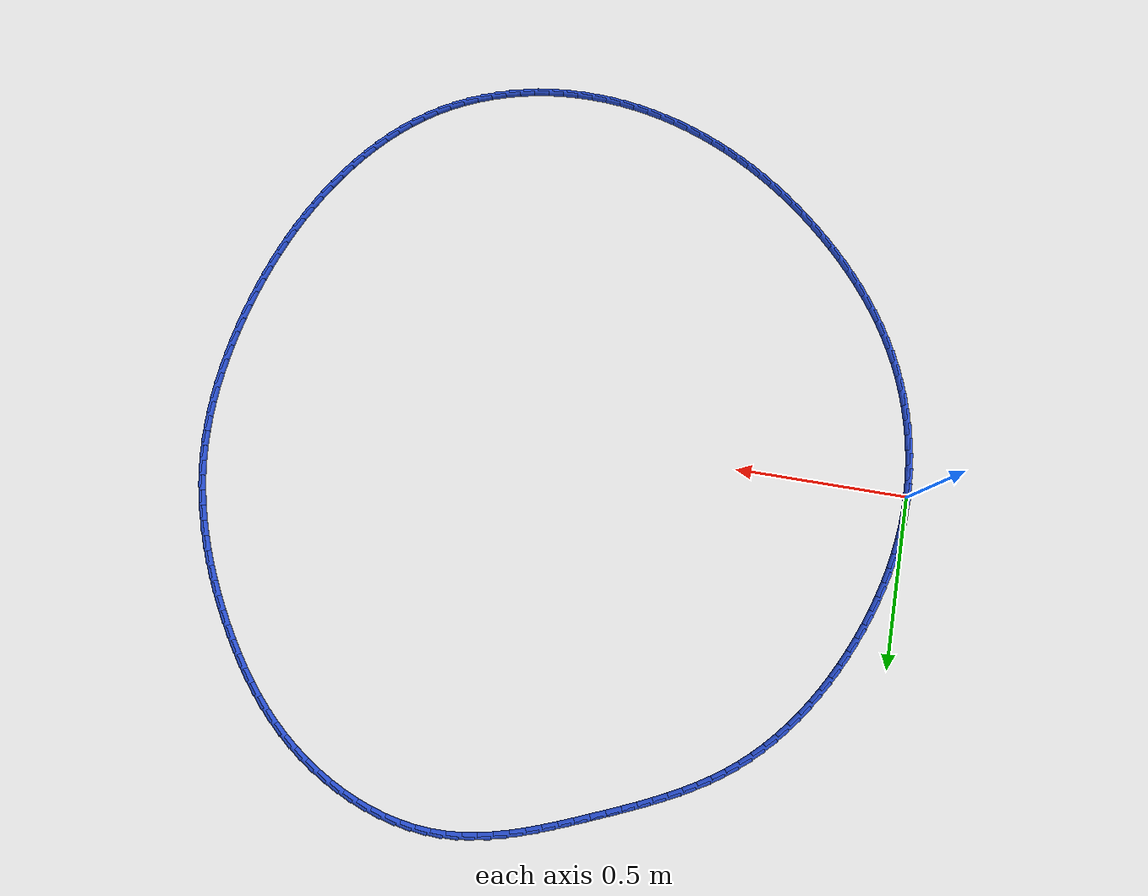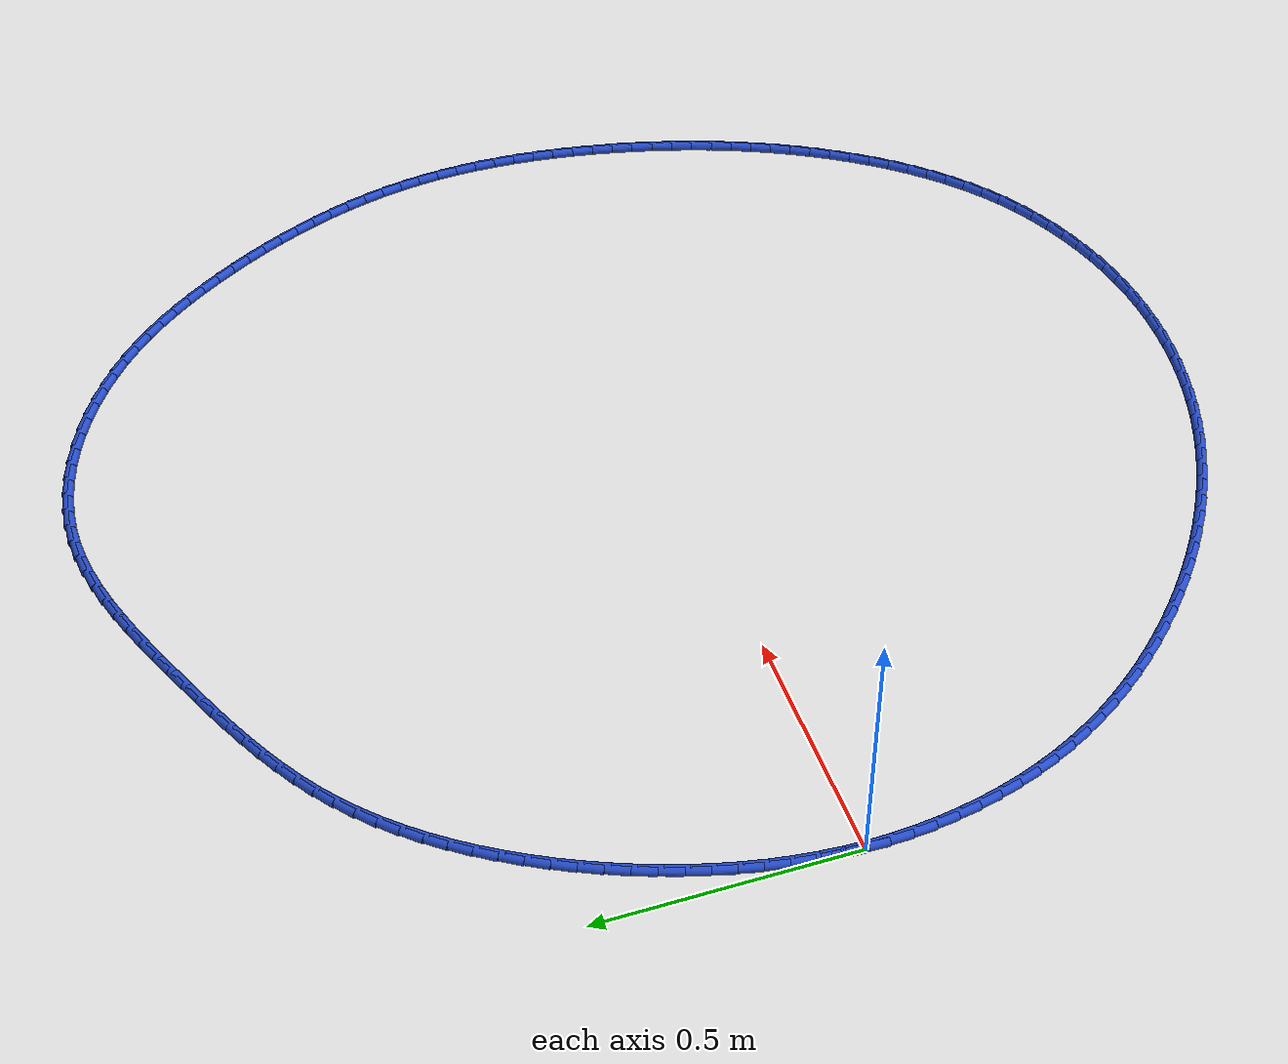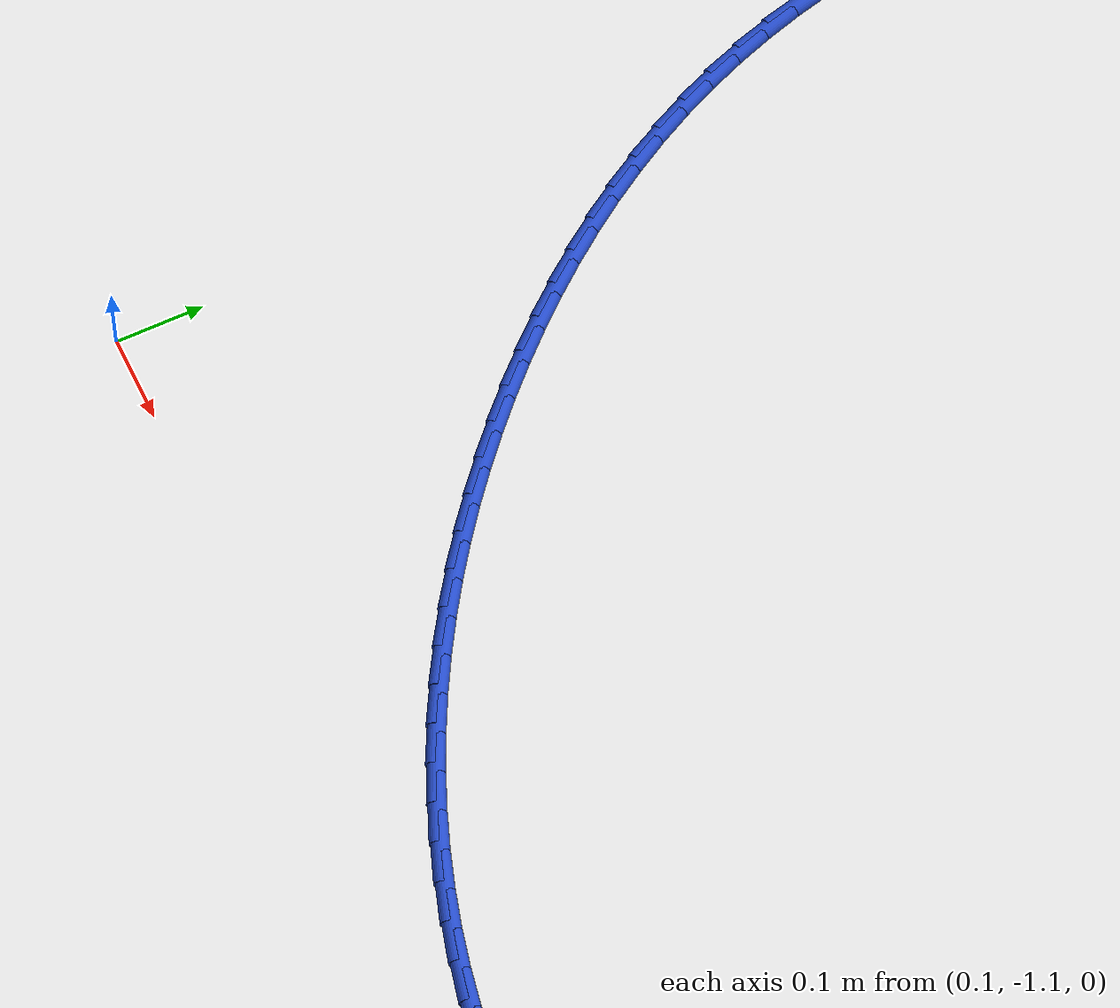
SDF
<sdf version="1.6">
 <world name="default">
  <light name="sun" type="directional">
   <pose>0 0 10 0 -0 0</pose>
   <diffuse>0.8 0.8 0.8 1</diffuse>
   <specular>0.2 0.2 0.2 1</specular>
   <attenuation>
    <range>1000</range>
    <constant>0.9</constant>
    <linear>0.01</linear>
    <quadratic>0.001</quadratic>
   </attenuation>
   <direction>-0.5 0.1 -0.9</direction>
  </light>
  <model name="ground_plane">
   <static>1</static>
   <link name="link">
    <collision name="collision">
     <geometry><plane><normal>0 0 1</normal><size>100 100</size></plane></geometry>
     <surface><friction><ode><mu>100</mu><mu2>50</mu2></ode></friction></surface>
    </collision>
    <visual name="visual">
     <cast_shadows>0</cast_shadows>
     <geometry><plane><normal>0 0 1</normal><size>100 100</size></plane></geometry>
     <material>
      <script><uri>file://media/materials/scripts/gazebo.material</uri><name>Gazebo/WhiteGlow</name></script>
     </material>
    </visual>
   </link>
  </model>
  <gravity>0 0 -9.8</gravity>
  <magnetic_field>6e-06 2.3e-05 -4.2e-05</magnetic_field>
  <atmosphere type="adiabatic"/>
  <physics name="default_physics" default="0" type="ode">
   <max_step_size>0.001</max_step_size>
   <real_time_factor>1</real_time_factor>
   <real_time_update_rate>1000</real_time_update_rate>
  </physics>
  <scene><ambient>0.4 0.4 0.4 1</ambient><background>0.7 0.7 0.7 1</background><shadows>1</shadows></scene>
  <spherical_coordinates>
   <surface_model>EARTH_WGS84</surface_model>
   <latitude_deg>0</latitude_deg>
   <longitude_deg>0</longitude_deg>
   <elevation>0</elevation>
   <heading_deg>0</heading_deg>
  </spherical_coordinates>
  <model name="line">
   <link name="link_0">
    <pose>1.0408340855860843e-17 2.220446049250313e-16 0.01 0 1.57 1.5392410968493917</pose>
    <collision name="collision">
     <geometry><cylinder><radius>0.01</radius><length>0.08</length></cylinder></geometry>
    </collision>
    <visual name="visual">
     <material>
      <script><name>Gazebo/Blue</name><uri>file://media/materials/scripts/gazebo.material</uri></script>
     </material>
     <geometry><cylinder><radius>0.01</radius><length>0.08</length></cylinder></geometry>
    </visual>
   </link>
   <link name="link_1">
    <pose>0.001398862178370712 0.04431588210363694 0.01 0 1.57 1.4932696431814405</pose>
    <collision name="collision">
     <geometry><cylinder><radius>0.01</radius><length>0.08</length></cylinder></geometry>
    </collision>
    <visual name="visual">
     <material>
      <script><name>Gazebo/Blue</name><uri>file://media/materials/scripts/gazebo.material</uri></script>
     </material>
     <geometry><cylinder><radius>0.01</radius><length>0.08</length></cylinder></geometry>
    </visual>
   </link>
   <link name="link_2">
    <pose>0.004828192716508468 0.08846142128943678 0.01 0 1.57 1.4487476840128644</pose>
    <collision name="collision">
     <geometry><cylinder><radius>0.01</radius><length>0.08</length></cylinder></geometry>
    </collision>
    <visual name="visual">
     <material>
      <script><name>Gazebo/Blue</name><uri>file://media/materials/scripts/gazebo.material</uri></script>
     </material>
     <geometry><cylinder><radius>0.01</radius><length>0.08</length></cylinder></geometry>
    </visual>
   </link>
   <link name="link_3">
    <pose>0.010218470899984242 0.13240691014067268 0.01 0 1.57 1.4057422438726748</pose>
    <collision name="collision">
     <geometry><cylinder><radius>0.01</radius><length>0.08</length></cylinder></geometry>
    </collision>
    <visual name="visual">
     <material>
      <script><name>Gazebo/Blue</name><uri>file://media/materials/scripts/gazebo.material</uri></script>
     </material>
     <geometry><cylinder><radius>0.01</radius><length>0.08</length></cylinder></geometry>
    </visual>
   </link>
   <link name="link_4">
    <pose>0.01750017601436904 0.17612264124061774 0.01 0 1.57 1.3642935634772129</pose>
    <collision name="collision">
     <geometry><cylinder><radius>0.01</radius><length>0.08</length></cylinder></geometry>
    </collision>
    <visual name="visual">
     <material>
      <script><name>Gazebo/Blue</name><uri>file://media/materials/scripts/gazebo.material</uri></script>
     </material>
     <geometry><cylinder><radius>0.01</radius><length>0.08</length></cylinder></geometry>
    </visual>
   </link>
   <link name="link_5">
    <pose>0.026603787345233842 0.21957890717254488 0.01 0 1.57 1.3244178832661933</pose>
    <collision name="collision">
     <geometry><cylinder><radius>0.01</radius><length>0.08</length></cylinder></geometry>
    </collision>
    <visual name="visual">
     <material>
      <script><name>Gazebo/Blue</name><uri>file://media/materials/scripts/gazebo.material</uri></script>
     </material>
     <geometry><cylinder><radius>0.01</radius><length>0.08</length></cylinder></geometry>
    </visual>
   </link>
   <link name="link_6">
    <pose>0.037459784178149644 0.2627460005197272 0.01 0 1.57 1.28611057775462</pose>
    <collision name="collision">
     <geometry><cylinder><radius>0.01</radius><length>0.08</length></cylinder></geometry>
    </collision>
    <visual name="visual">
     <material>
      <script><name>Gazebo/Blue</name><uri>file://media/materials/scripts/gazebo.material</uri></script>
     </material>
     <geometry><cylinder><radius>0.01</radius><length>0.08</length></cylinder></geometry>
    </visual>
   </link>
   <link name="link_7">
    <pose>0.049998645798687395 0.30559421386543756 0.01 0 1.57 1.2493493976437677</pose>
    <collision name="collision">
     <geometry><cylinder><radius>0.01</radius><length>0.08</length></cylinder></geometry>
    </collision>
    <visual name="visual">
     <material>
      <script><name>Gazebo/Blue</name><uri>file://media/materials/scripts/gazebo.material</uri></script>
     </material>
     <geometry><cylinder><radius>0.01</radius><length>0.08</length></cylinder></geometry>
    </visual>
   </link>
   <link name="link_8">
    <pose>0.06415085149241813 0.3480938397929491 0.01 0 1.57 1.2140976305341973</pose>
    <collision name="collision">
     <geometry><cylinder><radius>0.01</radius><length>0.08</length></cylinder></geometry>
    </collision>
    <visual name="visual">
     <material>
      <script><name>Gazebo/Blue</name><uri>file://media/materials/scripts/gazebo.material</uri></script>
     </material>
     <geometry><cylinder><radius>0.01</radius><length>0.08</length></cylinder></geometry>
    </visual>
   </link>
   <link name="link_9">
    <pose>0.07984688054491279 0.39021517088553487 0.01 0 1.57 1.1802191456416422</pose>
    <collision name="collision">
     <geometry><cylinder><radius>0.01</radius><length>0.08</length></cylinder></geometry>
    </collision>
    <visual name="visual">
     <material>
      <script><name>Gazebo/Blue</name><uri>file://media/materials/scripts/gazebo.material</uri></script>
     </material>
     <geometry><cylinder><radius>0.01</radius><length>0.08</length></cylinder></geometry>
    </visual>
   </link>
   <link name="link_10">
    <pose>0.09701985751825334 0.4319245098351208 0.01 0 1.57 1.1463386795100414</pose>
    <collision name="collision">
     <geometry><cylinder><radius>0.01</radius><length>0.08</length></cylinder></geometry>
    </collision>
    <visual name="visual">
     <material>
      <script><name>Gazebo/Blue</name><uri>file://media/materials/scripts/gazebo.material</uri></script>
     </material>
     <geometry><cylinder><radius>0.01</radius><length>0.08</length></cylinder></geometry>
    </visual>
   </link>
   <link name="link_11">
    <pose>0.11564169404886498 0.4731296564846304 0.01 0 1.57 1.1113007717614247</pose>
    <collision name="collision">
     <geometry><cylinder><radius>0.01</radius><length>0.08</length></cylinder></geometry>
    </collision>
    <visual name="visual">
     <material>
      <script><name>Gazebo/Blue</name><uri>file://media/materials/scripts/gazebo.material</uri></script>
     </material>
     <geometry><cylinder><radius>0.01</radius><length>0.08</length></cylinder></geometry>
    </visual>
   </link>
   <link name="link_12">
    <pose>0.1357137591400467 0.5136939798990691 0.01 0 1.57 1.0748833001247073</pose>
    <collision name="collision">
     <geometry><cylinder><radius>0.01</radius><length>0.08</length></cylinder></geometry>
    </collision>
    <visual name="visual">
     <material>
      <script><name>Gazebo/Blue</name><uri>file://media/materials/scripts/gazebo.material</uri></script>
     </material>
     <geometry><cylinder><radius>0.01</radius><length>0.08</length></cylinder></geometry>
    </visual>
   </link>
   <link name="link_13">
    <pose>0.15723815673653366 0.553479740625499 0.01 0 1.57 1.0368876005789145</pose>
    <collision name="collision">
     <geometry><cylinder><radius>0.01</radius><length>0.08</length></cylinder></geometry>
    </collision>
    <visual name="visual">
     <material>
      <script><name>Gazebo/Blue</name><uri>file://media/materials/scripts/gazebo.material</uri></script>
     </material>
     <geometry><cylinder><radius>0.01</radius><length>0.08</length></cylinder></geometry>
    </visual>
   </link>
   <link name="link_14">
    <pose>0.18021699078306103 0.5923491992109826 0.01 0 1.57 0.997114784701263</pose>
    <collision name="collision">
     <geometry><cylinder><radius>0.01</radius><length>0.08</length></cylinder></geometry>
    </collision>
    <visual name="visual">
     <material>
      <script><name>Gazebo/Blue</name><uri>file://media/materials/scripts/gazebo.material</uri></script>
     </material>
     <geometry><cylinder><radius>0.01</radius><length>0.08</length></cylinder></geometry>
    </visual>
   </link>
   <link name="link_15">
    <pose>0.204652365224364 0.6301646162025818 0.01 0 1.57 0.9553676352426698</pose>
    <collision name="collision">
     <geometry><cylinder><radius>0.01</radius><length>0.08</length></cylinder></geometry>
    </collision>
    <visual name="visual">
     <material>
      <script><name>Gazebo/Blue</name><uri>file://media/materials/scripts/gazebo.material</uri></script>
     </material>
     <geometry><cylinder><radius>0.01</radius><length>0.08</length></cylinder></geometry>
    </visual>
   </link>
   <link name="link_16">
    <pose>0.23054638400517774 0.6667882521473588 0.01 0 1.57 0.9114539082437486</pose>
    <collision name="collision">
     <geometry><cylinder><radius>0.01</radius><length>0.08</length></cylinder></geometry>
    </collision>
    <visual name="visual">
     <material>
      <script><name>Gazebo/Blue</name><uri>file://media/materials/scripts/gazebo.material</uri></script>
     </material>
     <geometry><cylinder><radius>0.01</radius><length>0.08</length></cylinder></geometry>
    </visual>
   </link>
   <link name="link_17">
    <pose>0.25790115107023753 0.7020823675923764 0.01 0 1.57 0.8651913218155416</pose>
    <collision name="collision">
     <geometry><cylinder><radius>0.01</radius><length>0.08</length></cylinder></geometry>
    </collision>
    <visual name="visual">
     <material>
      <script><name>Gazebo/Blue</name><uri>file://media/materials/scripts/gazebo.material</uri></script>
     </material>
     <geometry><cylinder><radius>0.01</radius><length>0.08</length></cylinder></geometry>
    </visual>
   </link>
   <link name="link_18">
    <pose>0.28671877036427856 0.7359092230846966 0.01 0 1.57 0.8164145035119497</pose>
    <collision name="collision">
     <geometry><cylinder><radius>0.01</radius><length>0.08</length></cylinder></geometry>
    </collision>
    <visual name="visual">
     <material>
      <script><name>Gazebo/Blue</name><uri>file://media/materials/scripts/gazebo.material</uri></script>
     </material>
     <geometry><cylinder><radius>0.01</radius><length>0.08</length></cylinder></geometry>
    </visual>
   </link>
   <link name="link_19">
    <pose>0.317001345832036 0.7681310791713813 0.01 0 1.57 0.7649840974503498</pose>
    <collision name="collision">
     <geometry><cylinder><radius>0.01</radius><length>0.08</length></cylinder></geometry>
    </collision>
    <visual name="visual">
     <material>
      <script><name>Gazebo/Blue</name><uri>file://media/materials/scripts/gazebo.material</uri></script>
     </material>
     <geometry><cylinder><radius>0.01</radius><length>0.08</length></cylinder></geometry>
    </visual>
   </link>
   <link name="link_20">
    <pose>0.3487509814182449 0.7986101963994929 0.01 0 1.57 0.710798066862894</pose>
    <collision name="collision">
     <geometry><cylinder><radius>0.01</radius><length>0.08</length></cylinder></geometry>
    </collision>
    <visual name="visual">
     <material>
      <script><name>Gazebo/Blue</name><uri>file://media/materials/scripts/gazebo.material</uri></script>
     </material>
     <geometry><cylinder><radius>0.01</radius><length>0.08</length></cylinder></geometry>
    </visual>
   </link>
   <link name="link_21">
    <pose>0.3819697810676408 0.827208835316094 0.01 0 1.57 0.6547103186259758</pose>
    <collision name="collision">
     <geometry><cylinder><radius>0.01</radius><length>0.08</length></cylinder></geometry>
    </collision>
    <visual name="visual">
     <material>
      <script><name>Gazebo/Blue</name><uri>file://media/materials/scripts/gazebo.material</uri></script>
     </material>
     <geometry><cylinder><radius>0.01</radius><length>0.08</length></cylinder></geometry>
    </visual>
   </link>
   <link name="link_22">
    <pose>0.41664439247683716 0.8538272732625697 0.01 0 1.57 0.6021983852947349</pose>
    <collision name="collision">
     <geometry><cylinder><radius>0.01</radius><length>0.08</length></cylinder></geometry>
    </collision>
    <visual name="visual">
     <material>
      <script><name>Gazebo/Blue</name><uri>file://media/materials/scripts/gazebo.material</uri></script>
     </material>
     <geometry><cylinder><radius>0.01</radius><length>0.08</length></cylinder></geometry>
    </visual>
   </link>
   <link name="link_23">
    <pose>0.452670189180328 0.8785902890907099 0.01 0 1.57 0.5555062727503012</pose>
    <collision name="collision">
     <geometry><cylinder><radius>0.01</radius><length>0.08</length></cylinder></geometry>
    </collision>
    <visual name="visual">
     <material>
      <script><name>Gazebo/Blue</name><uri>file://media/materials/scripts/gazebo.material</uri></script>
     </material>
     <geometry><cylinder><radius>0.01</radius><length>0.08</length></cylinder></geometry>
    </visual>
   </link>
   <link name="link_24">
    <pose>0.4899091587651343 0.9017047790386439 0.01 0 1.57 0.5147914372172068</pose>
    <collision name="collision">
     <geometry><cylinder><radius>0.01</radius><length>0.08</length></cylinder></geometry>
    </collision>
    <visual name="visual">
     <material>
      <script><name>Gazebo/Blue</name><uri>file://media/materials/scripts/gazebo.material</uri></script>
     </material>
     <geometry><cylinder><radius>0.01</radius><length>0.08</length></cylinder></geometry>
    </visual>
   </link>
   <link name="link_25">
    <pose>0.5282232391033058 0.9233777616253971 0.01 0 1.57 0.4800787779305284</pose>
    <collision name="collision">
     <geometry><cylinder><radius>0.01</radius><length>0.08</length></cylinder></geometry>
    </collision>
    <visual name="visual">
     <material>
      <script><name>Gazebo/Blue</name><uri>file://media/materials/scripts/gazebo.material</uri></script>
     </material>
     <geometry><cylinder><radius>0.01</radius><length>0.08</length></cylinder></geometry>
    </visual>
   </link>
   <link name="link_26">
    <pose>0.5674743680668917 0.9438162553699948 0.01 0 1.57 0.4513072331626924</pose>
    <collision name="collision">
     <geometry><cylinder><radius>0.01</radius><length>0.08</length></cylinder></geometry>
    </collision>
    <visual name="visual">
     <material>
      <script><name>Gazebo/Blue</name><uri>file://media/materials/scripts/gazebo.material</uri></script>
     </material>
     <geometry><cylinder><radius>0.01</radius><length>0.08</length></cylinder></geometry>
    </visual>
   </link>
   <link name="link_27">
    <pose>0.6075244835279412 0.9632272787914627 0.01 0 1.57 0.4283677527781234</pose>
    <collision name="collision">
     <geometry><cylinder><radius>0.01</radius><length>0.08</length></cylinder></geometry>
    </collision>
    <visual name="visual">
     <material>
      <script><name>Gazebo/Blue</name><uri>file://media/materials/scripts/gazebo.material</uri></script>
     </material>
     <geometry><cylinder><radius>0.01</radius><length>0.08</length></cylinder></geometry>
    </visual>
   </link>
   <link name="link_28">
    <pose>0.6482355233585038 0.9818178504088256 0.01 0 1.57 0.4111335537225085</pose>
    <collision name="collision">
     <geometry><cylinder><radius>0.01</radius><length>0.08</length></cylinder></geometry>
    </collision>
    <visual name="visual">
     <material>
      <script><name>Gazebo/Blue</name><uri>file://media/materials/scripts/gazebo.material</uri></script>
     </material>
     <geometry><cylinder><radius>0.01</radius><length>0.08</length></cylinder></geometry>
    </visual>
   </link>
   <link name="link_29">
    <pose>0.689469425430629 0.9997949887411095 0.01 0 1.57 0.39948251193025003</pose>
    <collision name="collision">
     <geometry><cylinder><radius>0.01</radius><length>0.08</length></cylinder></geometry>
    </collision>
    <visual name="visual">
     <material>
      <script><name>Gazebo/Blue</name><uri>file://media/materials/scripts/gazebo.material</uri></script>
     </material>
     <geometry><cylinder><radius>0.01</radius><length>0.08</length></cylinder></geometry>
    </visual>
   </link>
   <link name="link_30">
    <pose>0.731088127616366 1.0173657123073396 0.01 0 1.57 0.3932870985815125</pose>
    <collision name="collision">
     <geometry><cylinder><radius>0.01</radius><length>0.08</length></cylinder></geometry>
    </collision>
    <visual name="visual">
     <material>
      <script><name>Gazebo/Blue</name><uri>file://media/materials/scripts/gazebo.material</uri></script>
     </material>
     <geometry><cylinder><radius>0.01</radius><length>0.08</length></cylinder></geometry>
    </visual>
   </link>
   <link name="link_31">
    <pose>0.7729538633855513 1.0347359163906815 0.01 0 1.57 0.3886526555463868</pose>
    <collision name="collision">
     <geometry><cylinder><radius>0.01</radius><length>0.08</length></cylinder></geometry>
    </collision>
    <visual name="visual">
     <material>
      <script><name>Gazebo/Blue</name><uri>file://media/materials/scripts/gazebo.material</uri></script>
     </material>
     <geometry><cylinder><radius>0.01</radius><length>0.08</length></cylinder></geometry>
    </visual>
   </link>
   <link name="link_32">
    <pose>0.8149734389557599 1.051942125220628 0.01 0 1.57 0.37766717752340034</pose>
    <collision name="collision">
     <geometry><cylinder><radius>0.01</radius><length>0.08</length></cylinder></geometry>
    </collision>
    <visual name="visual">
     <material>
      <script><name>Gazebo/Blue</name><uri>file://media/materials/scripts/gazebo.material</uri></script>
     </material>
     <geometry><cylinder><radius>0.01</radius><length>0.08</length></cylinder></geometry>
    </visual>
   </link>
   <link name="link_33">
    <pose>0.8571454213301235 1.0686721831331472 0.01 0 1.57 0.3592560662570996</pose>
    <collision name="collision">
     <geometry><cylinder><radius>0.01</radius><length>0.08</length></cylinder></geometry>
    </collision>
    <visual name="visual">
     <material>
      <script><name>Gazebo/Blue</name><uri>file://media/materials/scripts/gazebo.material</uri></script>
     </material>
     <geometry><cylinder><radius>0.01</radius><length>0.08</length></cylinder></geometry>
    </visual>
   </link>
   <link name="link_34">
    <pose>0.8994796832107826 1.0845709741745557 0.01 0 1.57 0.3332159286313968</pose>
    <collision name="collision">
     <geometry><cylinder><radius>0.01</radius><length>0.08</length></cylinder></geometry>
    </collision>
    <visual name="visual">
     <material>
      <script><name>Gazebo/Blue</name><uri>file://media/materials/scripts/gazebo.material</uri></script>
     </material>
     <geometry><cylinder><radius>0.01</radius><length>0.08</length></cylinder></geometry>
    </visual>
   </link>
   <link name="link_35">
    <pose>0.9419860972998773 1.0992833823911694 0.01 0 1.57 0.29926924251223297</pose>
    <collision name="collision">
     <geometry><cylinder><radius>0.01</radius><length>0.08</length></cylinder></geometry>
    </collision>
    <visual name="visual">
     <material>
      <script><name>Gazebo/Blue</name><uri>file://media/materials/scripts/gazebo.material</uri></script>
     </material>
     <geometry><cylinder><radius>0.01</radius><length>0.08</length></cylinder></geometry>
    </visual>
   </link>
   <link name="link_36">
    <pose>0.9846745362995472 1.1124542918293043 0.01 0 1.57 0.2571055033875677</pose>
    <collision name="collision">
     <geometry><cylinder><radius>0.01</radius><length>0.08</length></cylinder></geometry>
    </collision>
    <visual name="visual">
     <material>
      <script><name>Gazebo/Blue</name><uri>file://media/materials/scripts/gazebo.material</uri></script>
     </material>
     <geometry><cylinder><radius>0.01</radius><length>0.08</length></cylinder></geometry>
    </visual>
   </link>
   <link name="link_37">
    <pose>1.0275548729119326 1.1237285865352769 0.01 0 1.57 0.20644350228924846</pose>
    <collision name="collision">
     <geometry><cylinder><radius>0.01</radius><length>0.08</length></cylinder></geometry>
    </collision>
    <visual name="visual">
     <material>
      <script><name>Gazebo/Blue</name><uri>file://media/materials/scripts/gazebo.material</uri></script>
     </material>
     <geometry><cylinder><radius>0.01</radius><length>0.08</length></cylinder></geometry>
    </visual>
   </link>
   <link name="link_38">
    <pose>1.0706369798391733 1.1327511505554029 0.01 0 1.57 0.14711968281365162</pose>
    <collision name="collision">
     <geometry><cylinder><radius>0.01</radius><length>0.08</length></cylinder></geometry>
    </collision>
    <visual name="visual">
     <material>
      <script><name>Gazebo/Blue</name><uri>file://media/materials/scripts/gazebo.material</uri></script>
     </material>
     <geometry><cylinder><radius>0.01</radius><length>0.08</length></cylinder></geometry>
    </visual>
   </link>
   <link name="link_39">
    <pose>1.1139307297834096 1.1391668679359988 0.01 0 1.57 0.07920277676388549</pose>
    <collision name="collision">
     <geometry><cylinder><radius>0.01</radius><length>0.08</length></cylinder></geometry>
    </collision>
    <visual name="visual">
     <material>
      <script><name>Gazebo/Blue</name><uri>file://media/materials/scripts/gazebo.material</uri></script>
     </material>
     <geometry><cylinder><radius>0.01</radius><length>0.08</length></cylinder></geometry>
    </visual>
   </link>
   <link name="link_40">
    <pose>1.157445995446781 1.1426206227233802 0.01 0 1.57 0.0032378913855431696</pose>
    <collision name="collision">
     <geometry><cylinder><radius>0.01</radius><length>0.08</length></cylinder></geometry>
    </collision>
    <visual name="visual">
     <material>
      <script><name>Gazebo/Blue</name><uri>file://media/materials/scripts/gazebo.material</uri></script>
     </material>
     <geometry><cylinder><radius>0.01</radius><length>0.08</length></cylinder></geometry>
    </visual>
   </link>
   <link name="link_41">
    <pose>1.2011907453894992 1.142762263967369 0.01 0 1.57 -0.07519388185587397</pose>
    <collision name="collision">
     <geometry><cylinder><radius>0.01</radius><length>0.08</length></cylinder></geometry>
    </collision>
    <visual name="visual">
     <material>
      <script><name>Gazebo/Blue</name><uri>file://media/materials/scripts/gazebo.material</uri></script>
     </material>
     <geometry><cylinder><radius>0.01</radius><length>0.08</length></cylinder></geometry>
    </visual>
   </link>
   <link name="link_42">
    <pose>1.2450911266674778 1.1394549882889167 0.01 0 1.57 -0.1493983646815262</pose>
    <collision name="collision">
     <geometry><cylinder><radius>0.01</radius><length>0.08</length></cylinder></geometry>
    </collision>
    <visual name="visual">
     <material>
      <script><name>Gazebo/Blue</name><uri>file://media/materials/scripts/gazebo.material</uri></script>
     </material>
     <geometry><cylinder><radius>0.01</radius><length>0.08</length></cylinder></geometry>
    </visual>
   </link>
   <link name="link_43">
    <pose>1.2889622522303597 1.1328515110252275 0.01 0 1.57 -0.21924797441721217</pose>
    <collision name="collision">
     <geometry><cylinder><radius>0.01</radius><length>0.08</length></cylinder></geometry>
    </collision>
    <visual name="visual">
     <material>
      <script><name>Gazebo/Blue</name><uri>file://media/materials/scripts/gazebo.material</uri></script>
     </material>
     <geometry><cylinder><radius>0.01</radius><length>0.08</length></cylinder></geometry>
    </visual>
   </link>
   <link name="link_44">
    <pose>1.3326113171237173 1.1231251932546988 0.01 0 1.57 -0.2851966350148642</pose>
    <collision name="collision">
     <geometry><cylinder><radius>0.01</radius><length>0.08</length></cylinder></geometry>
    </collision>
    <visual name="visual">
     <material>
      <script><name>Gazebo/Blue</name><uri>file://media/materials/scripts/gazebo.material</uri></script>
     </material>
     <geometry><cylinder><radius>0.01</radius><length>0.08</length></cylinder></geometry>
    </visual>
   </link>
   <link name="link_45">
    <pose>1.3758455163931238 1.1104493960557278 0.01 0 1.57 -0.34776281803627923</pose>
    <collision name="collision">
     <geometry><cylinder><radius>0.01</radius><length>0.08</length></cylinder></geometry>
    </collision>
    <visual name="visual">
     <material>
      <script><name>Gazebo/Blue</name><uri>file://media/materials/scripts/gazebo.material</uri></script>
     </material>
     <geometry><cylinder><radius>0.01</radius><length>0.08</length></cylinder></geometry>
    </visual>
   </link>
   <link name="link_46">
    <pose>1.4184720450841513 1.0949974805067113 0.01 0 1.57 -0.4074989562832908</pose>
    <collision name="collision">
     <geometry><cylinder><radius>0.01</radius><length>0.08</length></cylinder></geometry>
    </collision>
    <visual name="visual">
     <material>
      <script><name>Gazebo/Blue</name><uri>file://media/materials/scripts/gazebo.material</uri></script>
     </material>
     <geometry><cylinder><radius>0.01</radius><length>0.08</length></cylinder></geometry>
    </visual>
   </link>
   <link name="link_47">
    <pose>1.4602980982423721 1.0769428076860466 0.01 0 1.57 -0.46497277580109314</pose>
    <collision name="collision">
     <geometry><cylinder><radius>0.01</radius><length>0.08</length></cylinder></geometry>
    </collision>
    <visual name="visual">
     <material>
      <script><name>Gazebo/Blue</name><uri>file://media/materials/scripts/gazebo.material</uri></script>
     </material>
     <geometry><cylinder><radius>0.01</radius><length>0.08</length></cylinder></geometry>
    </visual>
   </link>
   <link name="link_48">
    <pose>1.5011308709133595 1.0564587386721311 0.01 0 1.57 -0.5207580547044445</pose>
    <collision name="collision">
     <geometry><cylinder><radius>0.01</radius><length>0.08</length></cylinder></geometry>
    </collision>
    <visual name="visual">
     <material>
      <script><name>Gazebo/Blue</name><uri>file://media/materials/scripts/gazebo.material</uri></script>
     </material>
     <geometry><cylinder><radius>0.01</radius><length>0.08</length></cylinder></geometry>
    </visual>
   </link>
   <link name="link_49">
    <pose>1.5407775581426861 1.0337186345433618 0.01 0 1.57 -0.575432439204022</pose>
    <collision name="collision">
     <geometry><cylinder><radius>0.01</radius><length>0.08</length></cylinder></geometry>
    </collision>
    <visual name="visual">
     <material>
      <script><name>Gazebo/Blue</name><uri>file://media/materials/scripts/gazebo.material</uri></script>
     </material>
     <geometry><cylinder><radius>0.01</radius><length>0.08</length></cylinder></geometry>
    </visual>
   </link>
   <link name="link_50">
    <pose>1.579045354975925 1.0088958563781354 0.01 0 1.57 -0.6295803828350084</pose>
    <collision name="collision">
     <geometry><cylinder><radius>0.01</radius><length>0.08</length></cylinder></geometry>
    </collision>
    <visual name="visual">
     <material>
      <script><name>Gazebo/Blue</name><uri>file://media/materials/scripts/gazebo.material</uri></script>
     </material>
     <geometry><cylinder><radius>0.01</radius><length>0.08</length></cylinder></geometry>
    </visual>
   </link>
   <link name="link_51">
    <pose>1.6157414564586476 0.9821637652548495 0.01 0 1.57 -0.6837782524924692</pose>
    <collision name="collision">
     <geometry><cylinder><radius>0.01</radius><length>0.08</length></cylinder></geometry>
    </collision>
    <visual name="visual">
     <material>
      <script><name>Gazebo/Blue</name><uri>file://media/materials/scripts/gazebo.material</uri></script>
     </material>
     <geometry><cylinder><radius>0.01</radius><length>0.08</length></cylinder></geometry>
    </visual>
   </link>
   <link name="link_52">
    <pose>1.6506750688113678 0.9536953328349882 0.01 0 1.57 -0.7372651429133686</pose>
    <collision name="collision">
     <geometry><cylinder><radius>0.01</radius><length>0.08</length></cylinder></geometry>
    </collision>
    <visual name="visual">
     <material>
      <script><name>Gazebo/Blue</name><uri>file://media/materials/scripts/gazebo.material</uri></script>
     </material>
     <geometry><cylinder><radius>0.01</radius><length>0.08</length></cylinder></geometry>
    </visual>
   </link>
   <link name="link_53">
    <pose>1.6837712802246347 0.9236410929512027 0.01 0 1.57 -0.7879894782428652</pose>
    <collision name="collision">
     <geometry><cylinder><radius>0.01</radius><length>0.08</length></cylinder></geometry>
    </collision>
    <visual name="visual">
     <material>
      <script><name>Gazebo/Blue</name><uri>file://media/materials/scripts/gazebo.material</uri></script>
     </material>
     <geometry><cylinder><radius>0.01</radius><length>0.08</length></cylinder></geometry>
    </visual>
   </link>
   <link name="link_54">
    <pose>1.7151320953452267 0.8921173237088621 0.01 0 1.57 -0.835459527815596</pose>
    <collision name="collision">
     <geometry><cylinder><radius>0.01</radius><length>0.08</length></cylinder></geometry>
    </collision>
    <visual name="visual">
     <material>
      <script><name>Gazebo/Blue</name><uri>file://media/materials/scripts/gazebo.material</uri></script>
     </material>
     <geometry><cylinder><radius>0.01</radius><length>0.08</length></cylinder></geometry>
    </visual>
   </link>
   <link name="link_55">
    <pose>1.7448744261204676 0.8592374167638056 0.01 0 1.57 -0.8794364145640197</pose>
    <collision name="collision">
     <geometry><cylinder><radius>0.01</radius><length>0.08</length></cylinder></geometry>
    </collision>
    <visual name="visual">
     <material>
      <script><name>Gazebo/Blue</name><uri>file://media/materials/scripts/gazebo.material</uri></script>
     </material>
     <geometry><cylinder><radius>0.01</radius><length>0.08</length></cylinder></geometry>
    </visual>
   </link>
   <link name="link_56">
    <pose>1.773115184497683 0.825114763771871 0.01 0 1.57 -0.9197658123125304</pose>
    <collision name="collision">
     <geometry><cylinder><radius>0.01</radius><length>0.08</length></cylinder></geometry>
    </collision>
    <visual name="visual">
     <material>
      <script><name>Gazebo/Blue</name><uri>file://media/materials/scripts/gazebo.material</uri></script>
     </material>
     <geometry><cylinder><radius>0.01</radius><length>0.08</length></cylinder></geometry>
    </visual>
   </link>
   <link name="link_57">
    <pose>1.7999712824241971 0.7898627563888967 0.01 0 1.57 -0.956364749484892</pose>
    <collision name="collision">
     <geometry><cylinder><radius>0.01</radius><length>0.08</length></cylinder></geometry>
    </collision>
    <visual name="visual">
     <material>
      <script><name>Gazebo/Blue</name><uri>file://media/materials/scripts/gazebo.material</uri></script>
     </material>
     <geometry><cylinder><radius>0.01</radius><length>0.08</length></cylinder></geometry>
    </visual>
   </link>
   <link name="link_58">
    <pose>1.8255596318473364 0.7535947862707214 0.01 0 1.57 -0.9892065368995056</pose>
    <collision name="collision">
     <geometry><cylinder><radius>0.01</radius><length>0.08</length></cylinder></geometry>
    </collision>
    <visual name="visual">
     <material>
      <script><name>Gazebo/Blue</name><uri>file://media/materials/scripts/gazebo.material</uri></script>
     </material>
     <geometry><cylinder><radius>0.01</radius><length>0.08</length></cylinder></geometry>
    </visual>
   </link>
   <link name="link_59">
    <pose>1.8499971447144254 0.7164242450731838 0.01 0 1.57 -1.0183910396995377</pose>
    <collision name="collision">
     <geometry><cylinder><radius>0.01</radius><length>0.08</length></cylinder></geometry>
    </collision>
    <visual name="visual">
     <material>
      <script><name>Gazebo/Blue</name><uri>file://media/materials/scripts/gazebo.material</uri></script>
     </material>
     <geometry><cylinder><radius>0.01</radius><length>0.08</length></cylinder></geometry>
    </visual>
   </link>
   <link name="link_60">
    <pose>1.8733970620508875 0.6784632202649494 0.01 0 1.57 -1.0462432376355992</pose>
    <collision name="collision">
     <geometry><cylinder><radius>0.01</radius><length>0.08</length></cylinder></geometry>
    </collision>
    <visual name="visual">
     <material>
      <script><name>Gazebo/Blue</name><uri>file://media/materials/scripts/gazebo.material</uri></script>
     </material>
     <geometry><cylinder><radius>0.01</radius><length>0.08</length></cylinder></geometry>
    </visual>
   </link>
   <link name="link_61">
    <pose>1.8957748370472771 0.6397890577311512 0.01 0 1.57 -1.07531748959148</pose>
    <collision name="collision">
     <geometry><cylinder><radius>0.01</radius><length>0.08</length></cylinder></geometry>
    </collision>
    <visual name="visual">
     <material>
      <script><name>Gazebo/Blue</name><uri>file://media/materials/scripts/gazebo.material</uri></script>
     </material>
     <geometry><cylinder><radius>0.01</radius><length>0.08</length></cylinder></geometry>
    </visual>
   </link>
   <link name="link_62">
    <pose>1.9170400833582022 0.600441501204424 0.01 0 1.57 -1.1058389275875127</pose>
    <collision name="collision">
     <geometry><cylinder><radius>0.01</radius><length>0.08</length></cylinder></geometry>
    </collision>
    <visual name="visual">
     <material>
      <script><name>Gazebo/Blue</name><uri>file://media/materials/scripts/gazebo.material</uri></script>
     </material>
     <geometry><cylinder><radius>0.01</radius><length>0.08</length></cylinder></geometry>
    </visual>
   </link>
   <link name="link_63">
    <pose>1.9370971302150808 0.5604584169933874 0.01 0 1.57 -1.1379091922488629</pose>
    <collision name="collision">
     <geometry><cylinder><radius>0.01</radius><length>0.08</length></cylinder></geometry>
    </collision>
    <visual name="visual">
     <material>
      <script><name>Gazebo/Blue</name><uri>file://media/materials/scripts/gazebo.material</uri></script>
     </material>
     <geometry><cylinder><radius>0.01</radius><length>0.08</length></cylinder></geometry>
    </visual>
   </link>
   <link name="link_64">
    <pose>1.9558503068493327 0.5198776714066606 0.01 0 1.57 -1.171627762367167</pose>
    <collision name="collision">
     <geometry><cylinder><radius>0.01</radius><length>0.08</length></cylinder></geometry>
    </collision>
    <visual name="visual">
     <material>
      <script><name>Gazebo/Blue</name><uri>file://media/materials/scripts/gazebo.material</uri></script>
     </material>
     <geometry><cylinder><radius>0.01</radius><length>0.08</length></cylinder></geometry>
    </visual>
   </link>
   <link name="link_65">
    <pose>1.973203942492377 0.47873713075286284 0.01 0 1.57 -1.2070897394157256</pose>
    <collision name="collision">
     <geometry><cylinder><radius>0.01</radius><length>0.08</length></cylinder></geometry>
    </collision>
    <visual name="visual">
     <material>
      <script><name>Gazebo/Blue</name><uri>file://media/materials/scripts/gazebo.material</uri></script>
     </material>
     <geometry><cylinder><radius>0.01</radius><length>0.08</length></cylinder></geometry>
    </visual>
   </link>
   <link name="link_66">
    <pose>1.9890623663756317 0.4370746613406134 0.01 0 1.57 -1.2443829851224995</pose>
    <collision name="collision">
     <geometry><cylinder><radius>0.01</radius><length>0.08</length></cylinder></geometry>
    </collision>
    <visual name="visual">
     <material>
      <script><name>Gazebo/Blue</name><uri>file://media/materials/scripts/gazebo.material</uri></script>
     </material>
     <geometry><cylinder><radius>0.01</radius><length>0.08</length></cylinder></geometry>
    </visual>
   </link>
   <link name="link_67">
    <pose>2.0033299077305164 0.3949281294785313 0.01 0 1.57 -1.2835845569482978</pose>
    <collision name="collision">
     <geometry><cylinder><radius>0.01</radius><length>0.08</length></cylinder></geometry>
    </collision>
    <visual name="visual">
     <material>
      <script><name>Gazebo/Blue</name><uri>file://media/materials/scripts/gazebo.material</uri></script>
     </material>
     <geometry><cylinder><radius>0.01</radius><length>0.08</length></cylinder></geometry>
    </visual>
   </link>
   <link name="link_68">
    <pose>2.0159108957884495 0.35233540147523634 0.01 0 1.57 -1.3247564225186355</pose>
    <collision name="collision">
     <geometry><cylinder><radius>0.01</radius><length>0.08</length></cylinder></geometry>
    </collision>
    <visual name="visual">
     <material>
      <script><name>Gazebo/Blue</name><uri>file://media/materials/scripts/gazebo.material</uri></script>
     </material>
     <geometry><cylinder><radius>0.01</radius><length>0.08</length></cylinder></geometry>
    </visual>
   </link>
   <link name="link_69">
    <pose>2.02670965978085 0.30933434363934764 0.01 0 1.57 -1.3679404936648845</pose>
    <collision name="collision">
     <geometry><cylinder><radius>0.01</radius><length>0.08</length></cylinder></geometry>
    </collision>
    <visual name="visual">
     <material>
      <script><name>Gazebo/Blue</name><uri>file://media/materials/scripts/gazebo.material</uri></script>
     </material>
     <geometry><cylinder><radius>0.01</radius><length>0.08</length></cylinder></geometry>
    </visual>
   </link>
   <link name="link_70">
    <pose>2.035630528939137 0.2659628222794845 0.01 0 1.57 -1.4130899864215327</pose>
    <collision name="collision">
     <geometry><cylinder><radius>0.01</radius><length>0.08</length></cylinder></geometry>
    </collision>
    <visual name="visual">
     <material>
      <script><name>Gazebo/Blue</name><uri>file://media/materials/scripts/gazebo.material</uri></script>
     </material>
     <geometry><cylinder><radius>0.01</radius><length>0.08</length></cylinder></geometry>
    </visual>
   </link>
   <link name="link_71">
    <pose>2.0425806023199025 0.22225907198138198 0.01 0 1.57 -1.458346068065153</pose>
    <collision name="collision">
     <geometry><cylinder><radius>0.01</radius><length>0.08</length></cylinder></geometry>
    </collision>
    <visual name="visual">
     <material>
      <script><name>Gazebo/Blue</name><uri>file://media/materials/scripts/gazebo.material</uri></script>
     </material>
     <geometry><cylinder><radius>0.01</radius><length>0.08</length></cylinder></geometry>
    </visual>
   </link>
   <link name="link_72">
    <pose>2.04754790508128 0.1782720872991668 0.01 0 1.57 -1.5015910224160887</pose>
    <collision name="collision">
     <geometry><cylinder><radius>0.01</radius><length>0.08</length></cylinder></geometry>
    </collision>
    <visual name="visual">
     <material>
      <script><name>Gazebo/Blue</name><uri>file://media/materials/scripts/gazebo.material</uri></script>
     </material>
     <geometry><cylinder><radius>0.01</radius><length>0.08</length></cylinder></geometry>
    </visual>
   </link>
   <link name="link_73">
    <pose>2.0506122970964804 0.13406307316918398 0.01 0 1.57 -1.542714310483269</pose>
    <collision name="collision">
     <geometry><cylinder><radius>0.01</radius><length>0.08</length></cylinder></geometry>
    </collision>
    <visual name="visual">
     <material>
      <script><name>Gazebo/Blue</name><uri>file://media/materials/scripts/gazebo.material</uri></script>
     </material>
     <geometry><cylinder><radius>0.01</radius><length>0.08</length></cylinder></geometry>
    </visual>
   </link>
   <link name="link_74">
    <pose>2.0518586007287807 0.0896938943425383 0.01 0 1.57 1.5598457863994017</pose>
    <collision name="collision">
     <geometry><cylinder><radius>0.01</radius><length>0.08</length></cylinder></geometry>
    </collision>
    <visual name="visual">
     <material>
      <script><name>Gazebo/Blue</name><uri>file://media/materials/scripts/gazebo.material</uri></script>
     </material>
     <geometry><cylinder><radius>0.01</radius><length>0.08</length></cylinder></geometry>
    </visual>
   </link>
   <link name="link_75">
    <pose>2.051371638341454 0.045226415570334785 0.01 0 1.57 1.5228506671445563</pose>
    <collision name="collision">
     <geometry><cylinder><radius>0.01</radius><length>0.08</length></cylinder></geometry>
    </collision>
    <visual name="visual">
     <material>
      <script><name>Gazebo/Blue</name><uri>file://media/materials/scripts/gazebo.material</uri></script>
     </material>
     <geometry><cylinder><radius>0.01</radius><length>0.08</length></cylinder></geometry>
    </visual>
   </link>
   <link name="link_76">
    <pose>2.049236232297777 0.0007225016036778772 0.01 0 1.57 1.4878228461478593</pose>
    <collision name="collision">
     <geometry><cylinder><radius>0.01</radius><length>0.08</length></cylinder></geometry>
    </collision>
    <visual name="visual">
     <material>
      <script><name>Gazebo/Blue</name><uri>file://media/materials/scripts/gazebo.material</uri></script>
     </material>
     <geometry><cylinder><radius>0.01</radius><length>0.08</length></cylinder></geometry>
    </visual>
   </link>
   <link name="link_77">
    <pose>2.045537204961025 -0.04375598280632711 0.01 0 1.57 1.4546801673039733</pose>
    <collision name="collision">
     <geometry><cylinder><radius>0.01</radius><length>0.08</length></cylinder></geometry>
    </collision>
    <visual name="visual">
     <material>
      <script><name>Gazebo/Blue</name><uri>file://media/materials/scripts/gazebo.material</uri></script>
     </material>
     <geometry><cylinder><radius>0.01</radius><length>0.08</length></cylinder></geometry>
    </visual>
   </link>
   <link name="link_78">
    <pose>2.0403593786944727 -0.08814717290857457 0.01 0 1.57 1.4233325325160264</pose>
    <collision name="collision">
     <geometry><cylinder><radius>0.01</radius><length>0.08</length></cylinder></geometry>
    </collision>
    <visual name="visual">
     <material>
      <script><name>Gazebo/Blue</name><uri>file://media/materials/scripts/gazebo.material</uri></script>
     </material>
     <geometry><cylinder><radius>0.01</radius><length>0.08</length></cylinder></geometry>
    </visual>
   </link>
   <link name="link_79">
    <pose>2.033787575861396 -0.13238920395196105 0.01 0 1.57 1.3936852293604927</pose>
    <collision name="collision">
     <geometry><cylinder><radius>0.01</radius><length>0.08</length></cylinder></geometry>
    </collision>
    <visual name="visual">
     <material>
      <script><name>Gazebo/Blue</name><uri>file://media/materials/scripts/gazebo.material</uri></script>
     </material>
     <geometry><cylinder><radius>0.01</radius><length>0.08</length></cylinder></geometry>
    </visual>
   </link>
   <link name="link_80">
    <pose>2.0259066188250703 -0.17642021118538026 0.01 0 1.57 1.3656415647858375</pose>
    <collision name="collision">
     <geometry><cylinder><radius>0.01</radius><length>0.08</length></cylinder></geometry>
    </collision>
    <visual name="visual">
     <material>
      <script><name>Gazebo/Blue</name><uri>file://media/materials/scripts/gazebo.material</uri></script>
     </material>
     <geometry><cylinder><radius>0.01</radius><length>0.08</length></cylinder></geometry>
    </visual>
   </link>
   <link name="link_81">
    <pose>2.0168013299487706 -0.22017832985772867 0.01 0 1.57 1.3390852209340411</pose>
    <collision name="collision">
     <geometry><cylinder><radius>0.01</radius><length>0.08</length></cylinder></geometry>
    </collision>
    <visual name="visual">
     <material>
      <script><name>Gazebo/Blue</name><uri>file://media/materials/scripts/gazebo.material</uri></script>
     </material>
     <geometry><cylinder><radius>0.01</radius><length>0.08</length></cylinder></geometry>
    </visual>
   </link>
   <link name="link_82">
    <pose>2.0065555651133558 -0.26360197127312135 0.01 0 1.57 1.312947510888873</pose>
    <collision name="collision">
     <geometry><cylinder><radius>0.01</radius><length>0.08</length></cylinder></geometry>
    </collision>
    <visual name="visual">
     <material>
      <script><name>Gazebo/Blue</name><uri>file://media/materials/scripts/gazebo.material</uri></script>
     </material>
     <geometry><cylinder><radius>0.01</radius><length>0.08</length></cylinder></geometry>
    </visual>
   </link>
   <link name="link_83">
    <pose>1.995204705727151 -0.3066433924414958 0.01 0 1.57 1.2857810042579194</pose>
    <collision name="collision">
     <geometry><cylinder><radius>0.01</radius><length>0.08</length></cylinder></geometry>
    </collision>
    <visual name="visual">
     <material>
      <script><name>Gazebo/Blue</name><uri>file://media/materials/scripts/gazebo.material</uri></script>
     </material>
     <geometry><cylinder><radius>0.01</radius><length>0.08</length></cylinder></geometry>
    </visual>
   </link>
   <link name="link_84">
    <pose>1.9827140108562167 -0.34927487933384654 0.01 0 1.57 1.25748112309744</pose>
    <collision name="collision">
     <geometry><cylinder><radius>0.01</radius><length>0.08</length></cylinder></geometry>
    </collision>
    <visual name="visual">
     <material>
      <script><name>Gazebo/Blue</name><uri>file://media/materials/scripts/gazebo.material</uri></script>
     </material>
     <geometry><cylinder><radius>0.01</radius><length>0.08</length></cylinder></geometry>
    </visual>
   </link>
   <link name="link_85">
    <pose>1.9690432576498473 -0.3914702837145178 0.01 0 1.57 1.2280629298244672</pose>
    <collision name="collision">
     <geometry><cylinder><radius>0.01</radius><length>0.08</length></cylinder></geometry>
    </collision>
    <visual name="visual">
     <material>
      <script><name>Gazebo/Blue</name><uri>file://media/materials/scripts/gazebo.material</uri></script>
     </material>
     <geometry><cylinder><radius>0.01</radius><length>0.08</length></cylinder></geometry>
    </visual>
   </link>
   <link name="link_86">
    <pose>1.9541522232573374 -0.43320345734785654 0.01 0 1.57 1.197550621876065</pose>
    <collision name="collision">
     <geometry><cylinder><radius>0.01</radius><length>0.08</length></cylinder></geometry>
    </collision>
    <visual name="visual">
     <material>
      <script><name>Gazebo/Blue</name><uri>file://media/materials/scripts/gazebo.material</uri></script>
     </material>
     <geometry><cylinder><radius>0.01</radius><length>0.08</length></cylinder></geometry>
    </visual>
   </link>
   <link name="link_87">
    <pose>1.9380006848279832 -0.47444825199820806 0.01 0 1.57 1.165978458710603</pose>
    <collision name="collision">
     <geometry><cylinder><radius>0.01</radius><length>0.08</length></cylinder></geometry>
    </collision>
    <visual name="visual">
     <material>
      <script><name>Gazebo/Blue</name><uri>file://media/materials/scripts/gazebo.material</uri></script>
     </material>
     <geometry><cylinder><radius>0.01</radius><length>0.08</length></cylinder></geometry>
    </visual>
   </link>
   <link name="link_88">
    <pose>1.9205484195110798 -0.5151785194299175 0.01 0 1.57 1.1333915462277837</pose>
    <collision name="collision">
     <geometry><cylinder><radius>0.01</radius><length>0.08</length></cylinder></geometry>
    </collision>
    <visual name="visual">
     <material>
      <script><name>Gazebo/Blue</name><uri>file://media/materials/scripts/gazebo.material</uri></script>
     </material>
     <geometry><cylinder><radius>0.01</radius><length>0.08</length></cylinder></geometry>
    </visual>
   </link>
   <link name="link_89">
    <pose>1.9017552044559218 -0.5553681114073317 0.01 0 1.57 1.0998464179583414</pose>
    <collision name="collision">
     <geometry><cylinder><radius>0.01</radius><length>0.08</length></cylinder></geometry>
    </collision>
    <visual name="visual">
     <material>
      <script><name>Gazebo/Blue</name><uri>file://media/materials/scripts/gazebo.material</uri></script>
     </material>
     <geometry><cylinder><radius>0.01</radius><length>0.08</length></cylinder></geometry>
    </visual>
   </link>
   <link name="link_90">
    <pose>1.8815808168118036 -0.5949908796947959 0.01 0 1.57 1.0654108947140168</pose>
    <collision name="collision">
     <geometry><cylinder><radius>0.01</radius><length>0.08</length></cylinder></geometry>
    </collision>
    <visual name="visual">
     <material>
      <script><name>Gazebo/Blue</name><uri>file://media/materials/scripts/gazebo.material</uri></script>
     </material>
     <geometry><cylinder><radius>0.01</radius><length>0.08</length></cylinder></geometry>
    </visual>
   </link>
   <link name="link_91">
    <pose>1.8599850482079427 -0.6340206077926513 0.01 0 1.57 1.0299053842386294</pose>
    <collision name="collision">
     <geometry><cylinder><radius>0.01</radius><length>0.08</length></cylinder></geometry>
    </collision>
    <visual name="visual">
     <material>
      <script><name>Gazebo/Blue</name><uri>file://media/materials/scripts/gazebo.material</uri></script>
     </material>
     <geometry><cylinder><radius>0.01</radius><length>0.08</length></cylinder></geometry>
    </visual>
   </link>
   <link name="link_92">
    <pose>1.8369350929634491 -0.6723961800277015 0.01 0 1.57 0.9925915368464495</pose>
    <collision name="collision">
     <geometry><cylinder><radius>0.01</radius><length>0.08</length></cylinder></geometry>
    </collision>
    <visual name="visual">
     <material>
      <script><name>Gazebo/Blue</name><uri>file://media/materials/scripts/gazebo.material</uri></script>
     </material>
     <geometry><cylinder><radius>0.01</radius><length>0.08</length></cylinder></geometry>
    </visual>
   </link>
   <link name="link_93">
    <pose>1.812417589313872 -0.7099648145049517 0.01 0 1.57 0.9531454325912401</pose>
    <collision name="collision">
     <geometry><cylinder><radius>0.01</radius><length>0.08</length></cylinder></geometry>
    </collision>
    <visual name="visual">
     <material>
      <script><name>Gazebo/Blue</name><uri>file://media/materials/scripts/gazebo.material</uri></script>
     </material>
     <geometry><cylinder><radius>0.01</radius><length>0.08</length></cylinder></geometry>
    </visual>
   </link>
   <link name="link_94">
    <pose>1.7864223295518693 -0.7465588598714217 0.01 0 1.57 0.9113439748198031</pose>
    <collision name="collision">
     <geometry><cylinder><radius>0.01</radius><length>0.08</length></cylinder></geometry>
    </collision>
    <visual name="visual">
     <material>
      <script><name>Gazebo/Blue</name><uri>file://media/materials/scripts/gazebo.material</uri></script>
     </material>
     <geometry><cylinder><radius>0.01</radius><length>0.08</length></cylinder></geometry>
    </visual>
   </link>
   <link name="link_95">
    <pose>1.7589391059700987 -0.7820106647741291 0.01 0 1.57 0.8669697278842804</pose>
    <collision name="collision">
     <geometry><cylinder><radius>0.01</radius><length>0.08</length></cylinder></geometry>
    </collision>
    <visual name="visual">
     <material>
      <script><name>Gazebo/Blue</name><uri>file://media/materials/scripts/gazebo.material</uri></script>
     </material>
     <geometry><cylinder><radius>0.01</radius><length>0.08</length></cylinder></geometry>
    </visual>
   </link>
   <link name="link_96">
    <pose>1.7299577108612183 -0.8161525778600913 0.01 0 1.57 0.819817705918496</pose>
    <collision name="collision">
     <geometry><cylinder><radius>0.01</radius><length>0.08</length></cylinder></geometry>
    </collision>
    <visual name="visual">
     <material>
      <script><name>Gazebo/Blue</name><uri>file://media/materials/scripts/gazebo.material</uri></script>
     </material>
     <geometry><cylinder><radius>0.01</radius><length>0.08</length></cylinder></geometry>
    </visual>
   </link>
   <link name="link_97">
    <pose>1.6994679365178853 -0.848816947776328 0.01 0 1.57 0.7697049483709716</pose>
    <collision name="collision">
     <geometry><cylinder><radius>0.01</radius><length>0.08</length></cylinder></geometry>
    </collision>
    <visual name="visual">
     <material>
      <script><name>Gazebo/Blue</name><uri>file://media/materials/scripts/gazebo.material</uri></script>
     </material>
     <geometry><cylinder><radius>0.01</radius><length>0.08</length></cylinder></geometry>
    </visual>
   </link>
   <link name="link_98">
    <pose>1.667459575232759 -0.8798361231698565 0.01 0 1.57 0.7164831499515188</pose>
    <collision name="collision">
     <geometry><cylinder><radius>0.01</radius><length>0.08</length></cylinder></geometry>
    </collision>
    <visual name="visual">
     <material>
      <script><name>Gazebo/Blue</name><uri>file://media/materials/scripts/gazebo.material</uri></script>
     </material>
     <geometry><cylinder><radius>0.01</radius><length>0.08</length></cylinder></geometry>
    </visual>
   </link>
   <link name="link_99">
    <pose>1.6339224192984951 -0.9090424526876957 0.01 0 1.57 0.6600543269737456</pose>
    <collision name="collision">
     <geometry><cylinder><radius>0.01</radius><length>0.08</length></cylinder></geometry>
    </collision>
    <visual name="visual">
     <material>
      <script><name>Gazebo/Blue</name><uri>file://media/materials/scripts/gazebo.material</uri></script>
     </material>
     <geometry><cylinder><radius>0.01</radius><length>0.08</length></cylinder></geometry>
    </visual>
   </link>
   <link name="link_100">
    <pose>1.5988462610077527 -0.9362682849768637 0.01 0 1.57 0.6003915514865957</pose>
    <collision name="collision">
     <geometry><cylinder><radius>0.01</radius><length>0.08</length></cylinder></geometry>
    </collision>
    <visual name="visual">
     <material>
      <script><name>Gazebo/Blue</name><uri>file://media/materials/scripts/gazebo.material</uri></script>
     </material>
     <geometry><cylinder><radius>0.01</radius><length>0.08</length></cylinder></geometry>
    </visual>
   </link>
   <link name="link_101">
    <pose>1.5622209753649672 -0.9613460493879717 0.01 0 1.57 0.5388593259229156</pose>
    <collision name="collision">
     <geometry><cylinder><radius>0.01</radius><length>0.08</length></cylinder></geometry>
    </collision>
    <visual name="visual">
     <material>
      <script><name>Gazebo/Blue</name><uri>file://media/materials/scripts/gazebo.material</uri></script>
     </material>
     <geometry><cylinder><radius>0.01</radius><length>0.08</length></cylinder></geometry>
    </visual>
   </link>
   <link name="link_102">
    <pose>1.5240794287395873 -0.9841501228367202 0.01 0 1.57 0.4789039142690714</pose>
    <collision name="collision">
     <geometry><cylinder><radius>0.01</radius><length>0.08</length></cylinder></geometry>
    </collision>
    <visual name="visual">
     <material>
      <script><name>Gazebo/Blue</name><uri>file://media/materials/scripts/gazebo.material</uri></script>
     </material>
     <geometry><cylinder><radius>0.01</radius><length>0.08</length></cylinder></geometry>
    </visual>
   </link>
   <link name="link_103">
    <pose>1.4845676975414648 -1.00466534361952 0.01 0 1.57 0.42093925634014656</pose>
    <collision name="collision">
     <geometry><cylinder><radius>0.01</radius><length>0.08</length></cylinder></geometry>
    </collision>
    <visual name="visual">
     <material>
      <script><name>Gazebo/Blue</name><uri>file://media/materials/scripts/gazebo.material</uri></script>
     </material>
     <geometry><cylinder><radius>0.01</radius><length>0.08</length></cylinder></geometry>
    </visual>
   </link>
   <link name="link_104">
    <pose>1.4438502730633782 -1.0228945178153797 0.01 0 1.57 0.364770989010184</pose>
    <collision name="collision">
     <geometry><cylinder><radius>0.01</radius><length>0.08</length></cylinder></geometry>
    </collision>
    <visual name="visual">
     <material>
      <script><name>Gazebo/Blue</name><uri>file://media/materials/scripts/gazebo.material</uri></script>
     </material>
     <geometry><cylinder><radius>0.01</radius><length>0.08</length></cylinder></geometry>
    </visual>
   </link>
   <link name="link_105">
    <pose>1.4020916465981048 -1.038840451503309 0.01 0 1.57 0.3101750179361967</pose>
    <collision name="collision">
     <geometry><cylinder><radius>0.01</radius><length>0.08</length></cylinder></geometry>
    </collision>
    <visual name="visual">
     <material>
      <script><name>Gazebo/Blue</name><uri>file://media/materials/scripts/gazebo.material</uri></script>
     </material>
     <geometry><cylinder><radius>0.01</radius><length>0.08</length></cylinder></geometry>
    </visual>
   </link>
   <link name="link_106">
    <pose>1.359456309438425 -1.0525059507623171 0.01 0 1.57 0.25690552353481694</pose>
    <collision name="collision">
     <geometry><cylinder><radius>0.01</radius><length>0.08</length></cylinder></geometry>
    </collision>
    <visual name="visual">
     <material>
      <script><name>Gazebo/Blue</name><uri>file://media/materials/scripts/gazebo.material</uri></script>
     </material>
     <geometry><cylinder><radius>0.01</radius><length>0.08</length></cylinder></geometry>
    </visual>
   </link>
   <link name="link_107">
    <pose>1.316108752877114 -1.063893821671413 0.01 0 1.57 0.20470092172219218</pose>
    <collision name="collision">
     <geometry><cylinder><radius>0.01</radius><length>0.08</length></cylinder></geometry>
    </collision>
    <visual name="visual">
     <material>
      <script><name>Gazebo/Blue</name><uri>file://media/materials/scripts/gazebo.material</uri></script>
     </material>
     <geometry><cylinder><radius>0.01</radius><length>0.08</length></cylinder></geometry>
    </visual>
   </link>
   <link name="link_108">
    <pose>1.2722134682069532 -1.073006870309607 0.01 0 1.57 0.15328801321063026</pose>
    <collision name="collision">
     <geometry><cylinder><radius>0.01</radius><length>0.08</length></cylinder></geometry>
    </collision>
    <visual name="visual">
     <material>
      <script><name>Gazebo/Blue</name><uri>file://media/materials/scripts/gazebo.material</uri></script>
     </material>
     <geometry><cylinder><radius>0.01</radius><length>0.08</length></cylinder></geometry>
    </visual>
   </link>
   <link name="link_109">
    <pose>1.2279349467207203 -1.0798479027559065 0.01 0 1.57 0.10238998257643007</pose>
    <collision name="collision">
     <geometry><cylinder><radius>0.01</radius><length>0.08</length></cylinder></geometry>
    </collision>
    <visual name="visual">
     <material>
      <script><name>Gazebo/Blue</name><uri>file://media/materials/scripts/gazebo.material</uri></script>
     </material>
     <geometry><cylinder><radius>0.01</radius><length>0.08</length></cylinder></geometry>
    </visual>
   </link>
   <link name="link_110">
    <pose>1.1834372311063177 -1.084420011813363 0.01 0 1.57 0.052117473333303466</pose>
    <collision name="collision">
     <geometry><cylinder><radius>0.01</radius><length>0.08</length></cylinder></geometry>
    </collision>
    <visual name="visual">
     <material>
      <script><name>Gazebo/Blue</name><uri>file://media/materials/scripts/gazebo.material</uri></script>
     </material>
     <geometry><cylinder><radius>0.01</radius><length>0.08</length></cylinder></geometry>
    </visual>
   </link>
   <link name="link_111">
    <pose>1.1388540240367888 -1.0867456819861498 0.01 0 1.57 0.0029854417208971034</pose>
    <collision name="collision">
     <geometry><cylinder><radius>0.01</radius><length>0.08</length></cylinder></geometry>
    </collision>
    <visual name="visual">
     <material>
      <script><name>Gazebo/Blue</name><uri>file://media/materials/scripts/gazebo.material</uri></script>
     </material>
     <geometry><cylinder><radius>0.01</radius><length>0.08</length></cylinder></geometry>
    </visual>
   </link>
   <link name="link_112">
    <pose>1.094269919144714 -1.0868787856284285 0.01 0 1.57 -0.04496986044049373</pose>
    <collision name="collision">
     <geometry><cylinder><radius>0.01</radius><length>0.08</length></cylinder></geometry>
    </collision>
    <visual name="visual">
     <material>
      <script><name>Gazebo/Blue</name><uri>file://media/materials/scripts/gazebo.material</uri></script>
     </material>
     <geometry><cylinder><radius>0.01</radius><length>0.08</length></cylinder></geometry>
    </visual>
   </link>
   <link name="link_113">
    <pose>1.0497650325548897 -1.0848760568758453 0.01 0 1.57 -0.09178727896651195</pose>
    <collision name="collision">
     <geometry><cylinder><radius>0.01</radius><length>0.08</length></cylinder></geometry>
    </collision>
    <visual name="visual">
     <material>
      <script><name>Gazebo/Blue</name><uri>file://media/materials/scripts/gazebo.material</uri></script>
     </material>
     <geometry><cylinder><radius>0.01</radius><length>0.08</length></cylinder></geometry>
    </visual>
   </link>
   <link name="link_114">
    <pose>1.0054194803921137 -1.0807942298640447 0.01 0 1.57 -0.13752427889111135</pose>
    <collision name="collision">
     <geometry><cylinder><radius>0.01</radius><length>0.08</length></cylinder></geometry>
    </collision>
    <visual name="visual">
     <material>
      <script><name>Gazebo/Blue</name><uri>file://media/materials/scripts/gazebo.material</uri></script>
     </material>
     <geometry><cylinder><radius>0.01</radius><length>0.08</length></cylinder></geometry>
    </visual>
   </link>
   <link name="link_115">
    <pose>0.961313378781181 -1.074690038728671 0.01 0 1.57 -0.18225402316163522</pose>
    <collision name="collision">
     <geometry><cylinder><radius>0.01</radius><length>0.08</length></cylinder></geometry>
    </collision>
    <visual name="visual">
     <material>
      <script><name>Gazebo/Blue</name><uri>file://media/materials/scripts/gazebo.material</uri></script>
     </material>
     <geometry><cylinder><radius>0.01</radius><length>0.08</length></cylinder></geometry>
    </visual>
   </link>
   <link name="link_116">
    <pose>0.9175268438468894 -1.066620217605371 0.01 0 1.57 -0.22606271803160258</pose>
    <collision name="collision">
     <geometry><cylinder><radius>0.01</radius><length>0.08</length></cylinder></geometry>
    </collision>
    <visual name="visual">
     <material>
      <script><name>Gazebo/Blue</name><uri>file://media/materials/scripts/gazebo.material</uri></script>
     </material>
     <geometry><cylinder><radius>0.01</radius><length>0.08</length></cylinder></geometry>
    </visual>
   </link>
   <link name="link_117">
    <pose>0.874139991714036 -1.056641500629788 0.01 0 1.57 -0.2690472915916321</pose>
    <collision name="collision">
     <geometry><cylinder><radius>0.01</radius><length>0.08</length></cylinder></geometry>
    </collision>
    <visual name="visual">
     <material>
      <script><name>Gazebo/Blue</name><uri>file://media/materials/scripts/gazebo.material</uri></script>
     </material>
     <geometry><cylinder><radius>0.01</radius><length>0.08</length></cylinder></geometry>
    </visual>
   </link>
   <link name="link_118">
    <pose>0.8312329385074164 -1.0448106219375686 0.01 0 1.57 -0.311297195166308</pose>
    <collision name="collision">
     <geometry><cylinder><radius>0.01</radius><length>0.08</length></cylinder></geometry>
    </collision>
    <visual name="visual">
     <material>
      <script><name>Gazebo/Blue</name><uri>file://media/materials/scripts/gazebo.material</uri></script>
     </material>
     <geometry><cylinder><radius>0.01</radius><length>0.08</length></cylinder></geometry>
    </visual>
   </link>
   <link name="link_119">
    <pose>0.7888839482860378 -1.031184478583545 0.01 0 1.57 -0.3526699904663226</pose>
    <collision name="collision">
     <geometry><cylinder><radius>0.01</radius><length>0.08</length></cylinder></geometry>
    </collision>
    <visual name="visual">
     <material>
      <script><name>Gazebo/Blue</name><uri>file://media/materials/scripts/gazebo.material</uri></script>
     </material>
     <geometry><cylinder><radius>0.01</radius><length>0.08</length></cylinder></geometry>
    </visual>
   </link>
   <link name="link_120">
    <pose>0.7471452676798036 -1.0158222562768873 0.01 0 1.57 -0.39301450188713155</pose>
    <collision name="collision">
     <geometry><cylinder><radius>0.01</radius><length>0.08</length></cylinder></geometry>
    </collision>
    <visual name="visual">
     <material>
      <script><name>Gazebo/Blue</name><uri>file://media/materials/scripts/gazebo.material</uri></script>
     </material>
     <geometry><cylinder><radius>0.01</radius><length>0.08</length></cylinder></geometry>
    </visual>
   </link>
   <link name="link_121">
    <pose>0.7060499480135931 -0.9987848292647831 0.01 0 1.57 -0.43233905895975966</pose>
    <collision name="collision">
     <geometry><cylinder><radius>0.01</radius><length>0.08</length></cylinder></geometry>
    </collision>
    <visual name="visual">
     <material>
      <script><name>Gazebo/Blue</name><uri>file://media/materials/scripts/gazebo.material</uri></script>
     </material>
     <geometry><cylinder><radius>0.01</radius><length>0.08</length></cylinder></geometry>
    </visual>
   </link>
   <link name="link_122">
    <pose>0.6656305926482124 -0.9801331112001158 0.01 0 1.57 -0.47066773452963323</pose>
    <collision name="collision">
     <geometry><cylinder><radius>0.01</radius><length>0.08</length></cylinder></geometry>
    </collision>
    <visual name="visual">
     <material>
      <script><name>Gazebo/Blue</name><uri>file://media/materials/scripts/gazebo.material</uri></script>
     </material>
     <geometry><cylinder><radius>0.01</radius><length>0.08</length></cylinder></geometry>
    </visual>
   </link>
   <link name="link_123">
    <pose>0.6259198049444652 -0.9599280157357697 0.01 0 1.57 -0.5080347760303535</pose>
    <collision name="collision">
     <geometry><cylinder><radius>0.01</radius><length>0.08</length></cylinder></geometry>
    </collision>
    <visual name="visual">
     <material>
      <script><name>Gazebo/Blue</name><uri>file://media/materials/scripts/gazebo.material</uri></script>
     </material>
     <geometry><cylinder><radius>0.01</radius><length>0.08</length></cylinder></geometry>
    </visual>
   </link>
   <link name="link_124">
    <pose>0.5869501882631573 -0.9382304565246278 0.01 0 1.57 -0.5444830554800137</pose>
    <collision name="collision">
     <geometry><cylinder><radius>0.01</radius><length>0.08</length></cylinder></geometry>
    </collision>
    <visual name="visual">
     <material>
      <script><name>Gazebo/Blue</name><uri>file://media/materials/scripts/gazebo.material</uri></script>
     </material>
     <geometry><cylinder><radius>0.01</radius><length>0.08</length></cylinder></geometry>
    </visual>
   </link>
   <link name="link_125">
    <pose>0.5487543459650945 -0.9151013472195745 0.01 0 1.57 -0.5800626533729011</pose>
    <collision name="collision">
     <geometry><cylinder><radius>0.01</radius><length>0.08</length></cylinder></geometry>
    </collision>
    <visual name="visual">
     <material>
      <script><name>Gazebo/Blue</name><uri>file://media/materials/scripts/gazebo.material</uri></script>
     </material>
     <geometry><cylinder><radius>0.01</radius><length>0.08</length></cylinder></geometry>
    </visual>
   </link>
   <link name="link_126">
    <pose>0.5113648814110806 -0.8906016014734931 0.01 0 1.57 -0.6148296025324094</pose>
    <collision name="collision">
     <geometry><cylinder><radius>0.01</radius><length>0.08</length></cylinder></geometry>
    </collision>
    <visual name="visual">
     <material>
      <script><name>Gazebo/Blue</name><uri>file://media/materials/scripts/gazebo.material</uri></script>
     </material>
     <geometry><cylinder><radius>0.01</radius><length>0.08</length></cylinder></geometry>
    </visual>
   </link>
   <link name="link_127">
    <pose>0.47481439796192226 -0.8647921329392679 0.01 0 1.57 -0.6488448045697356</pose>
    <collision name="collision">
     <geometry><cylinder><radius>0.01</radius><length>0.08</length></cylinder></geometry>
    </collision>
    <visual name="visual">
     <material>
      <script><name>Gazebo/Blue</name><uri>file://media/materials/scripts/gazebo.material</uri></script>
     </material>
     <geometry><cylinder><radius>0.01</radius><length>0.08</length></cylinder></geometry>
    </visual>
   </link>
   <link name="link_128">
    <pose>0.4391354989784231 -0.8377338552697816 0.01 0 1.57 -0.6821731213130249</pose>
    <collision name="collision">
     <geometry><cylinder><radius>0.01</radius><length>0.08</length></cylinder></geometry>
    </collision>
    <visual name="visual">
     <material>
      <script><name>Gazebo/Blue</name><uri>file://media/materials/scripts/gazebo.material</uri></script>
     </material>
     <geometry><cylinder><radius>0.01</radius><length>0.08</length></cylinder></geometry>
    </visual>
   </link>
   <link name="link_129">
    <pose>0.4043607878213891 -0.8094876821179189 0.01 0 1.57 -0.7148826361818309</pose>
    <collision name="collision">
     <geometry><cylinder><radius>0.01</radius><length>0.08</length></cylinder></geometry>
    </collision>
    <visual name="visual">
     <material>
      <script><name>Gazebo/Blue</name><uri>file://media/materials/scripts/gazebo.material</uri></script>
     </material>
     <geometry><cylinder><radius>0.01</radius><length>0.08</length></cylinder></geometry>
    </visual>
   </link>
   <link name="link_130">
    <pose>0.37052286785162597 -0.7801145271365635 0.01 0 1.57 -0.7470440755599901</pose>
    <collision name="collision">
     <geometry><cylinder><radius>0.01</radius><length>0.08</length></cylinder></geometry>
    </collision>
    <visual name="visual">
     <material>
      <script><name>Gazebo/Blue</name><uri>file://media/materials/scripts/gazebo.material</uri></script>
     </material>
     <geometry><cylinder><radius>0.01</radius><length>0.08</length></cylinder></geometry>
    </visual>
   </link>
   <link name="link_131">
    <pose>0.33765434242993764 -0.7496753039785987 0.01 0 1.57 -0.7788896492252085</pose>
    <collision name="collision">
     <geometry><cylinder><radius>0.01</radius><length>0.08</length></cylinder></geometry>
    </collision>
    <visual name="visual">
     <material>
      <script><name>Gazebo/Blue</name><uri>file://media/materials/scripts/gazebo.material</uri></script>
     </material>
     <geometry><cylinder><radius>0.01</radius><length>0.08</length></cylinder></geometry>
    </visual>
   </link>
   <link name="link_132">
    <pose>0.3057929884202016 -0.718226014010908 0.01 0 1.57 -0.8117137808547171</pose>
    <collision name="collision">
     <geometry><cylinder><radius>0.01</radius><length>0.08</length></cylinder></geometry>
    </collision>
    <visual name="visual">
     <material>
      <script><name>Gazebo/Blue</name><uri>file://media/materials/scripts/gazebo.material</uri></script>
     </material>
     <geometry><cylinder><radius>0.01</radius><length>0.08</length></cylinder></geometry>
    </visual>
   </link>
   <link name="link_133">
    <pose>0.2750161049472994 -0.6857851318710414 0.01 0 1.57 -0.8461599574210182</pose>
    <collision name="collision">
     <geometry><cylinder><radius>0.01</radius><length>0.08</length></cylinder></geometry>
    </collision>
    <visual name="visual">
     <material>
      <script><name>Gazebo/Blue</name><uri>file://media/materials/scripts/gazebo.material</uri></script>
     </material>
     <geometry><cylinder><radius>0.01</radius><length>0.08</length></cylinder></geometry>
    </visual>
   </link>
   <link name="link_134">
    <pose>0.2454192215114665 -0.6523538222971635 0.01 0 1.57 -0.8823078926207711</pose>
    <collision name="collision">
     <geometry><cylinder><radius>0.01</radius><length>0.08</length></cylinder></geometry>
    </collision>
    <visual name="visual">
     <material>
      <script><name>Gazebo/Blue</name><uri>file://media/materials/scripts/gazebo.material</uri></script>
     </material>
     <geometry><cylinder><radius>0.01</radius><length>0.08</length></cylinder></geometry>
    </visual>
   </link>
   <link name="link_135">
    <pose>0.2170979652696681 -0.6179331573015299 0.01 0 1.57 -0.920224491978351</pose>
    <collision name="collision">
     <geometry><cylinder><radius>0.01</radius><length>0.08</length></cylinder></geometry>
    </collision>
    <visual name="visual">
     <material>
      <script><name>Gazebo/Blue</name><uri>file://media/materials/scripts/gazebo.material</uri></script>
     </material>
     <geometry><cylinder><radius>0.01</radius><length>0.08</length></cylinder></geometry>
    </visual>
   </link>
   <link name="link_136">
    <pose>0.19014796337886772 -0.5825242088963933 0.01 0 1.57 -0.9599632619835224</pose>
    <collision name="collision">
     <geometry><cylinder><radius>0.01</radius><length>0.08</length></cylinder></geometry>
    </collision>
    <visual name="visual">
     <material>
      <script><name>Gazebo/Blue</name><uri>file://media/materials/scripts/gazebo.material</uri></script>
     </material>
     <geometry><cylinder><radius>0.01</radius><length>0.08</length></cylinder></geometry>
    </visual>
   </link>
   <link name="link_137">
    <pose>0.1646648429960303 -0.5461280490940085 0.01 0 1.57 -1.001560183467063</pose>
    <collision name="collision">
     <geometry><cylinder><radius>0.01</radius><length>0.08</length></cylinder></geometry>
    </collision>
    <visual name="visual">
     <material>
      <script><name>Gazebo/Blue</name><uri>file://media/materials/scripts/gazebo.material</uri></script>
     </material>
     <geometry><cylinder><radius>0.01</radius><length>0.08</length></cylinder></geometry>
    </visual>
   </link>
   <link name="link_138">
    <pose>0.14074423127812083 -0.5087457499066305 0.01 0 1.57 -1.0450291603119304</pose>
    <collision name="collision">
     <geometry><cylinder><radius>0.01</radius><length>0.08</length></cylinder></geometry>
    </collision>
    <visual name="visual">
     <material>
      <script><name>Gazebo/Blue</name><uri>file://media/materials/scripts/gazebo.material</uri></script>
     </material>
     <geometry><cylinder><radius>0.01</radius><length>0.08</length></cylinder></geometry>
    </visual>
   </link>
   <link name="link_139">
    <pose>0.11848175538210295 -0.4703783833465121 0.01 0 1.57 -1.0903572330543458</pose>
    <collision name="collision">
     <geometry><cylinder><radius>0.01</radius><length>0.08</length></cylinder></geometry>
    </collision>
    <visual name="visual">
     <material>
      <script><name>Gazebo/Blue</name><uri>file://media/materials/scripts/gazebo.material</uri></script>
     </material>
     <geometry><cylinder><radius>0.01</radius><length>0.08</length></cylinder></geometry>
    </visual>
   </link>
   <link name="link_140">
    <pose>0.09797304246494196 -0.431027021425909 0.01 0 1.57 -1.1374726228411352</pose>
    <collision name="collision">
     <geometry><cylinder><radius>0.01</radius><length>0.08</length></cylinder></geometry>
    </collision>
    <visual name="visual">
     <material>
      <script><name>Gazebo/Blue</name><uri>file://media/materials/scripts/gazebo.material</uri></script>
     </material>
     <geometry><cylinder><radius>0.01</radius><length>0.08</length></cylinder></geometry>
    </visual>
   </link>
   <link name="link_141">
    <pose>0.07931294895236828 -0.39069395159256975 0.01 0 1.57 -1.18524441535965</pose>
    <collision name="collision">
     <geometry><cylinder><radius>0.01</radius><length>0.08</length></cylinder></geometry>
    </collision>
    <visual name="visual">
     <material>
      <script><name>Gazebo/Blue</name><uri>file://media/materials/scripts/gazebo.material</uri></script>
     </material>
     <geometry><cylinder><radius>0.01</radius><length>0.08</length></cylinder></geometry>
    </visual>
   </link>
   <link name="link_142">
    <pose>0.06256543940365895 -0.3494301774606517 0.01 0 1.57 -1.2323469507637828</pose>
    <collision name="collision">
     <geometry><cylinder><radius>0.01</radius><length>0.08</length></cylinder></geometry>
    </collision>
    <visual name="visual">
     <material>
      <script><name>Gazebo/Blue</name><uri>file://media/materials/scripts/gazebo.material</uri></script>
     </material>
     <geometry><cylinder><radius>0.01</radius><length>0.08</length></cylinder></geometry>
    </visual>
   </link>
   <link name="link_143">
    <pose>0.04775380247090894 -0.30735084814571606 0.01 0 1.57 -1.278853994697495</pose>
    <collision name="collision">
     <geometry><cylinder><radius>0.01</radius><length>0.08</length></cylinder></geometry>
    </collision>
    <visual name="visual">
     <material>
      <script><name>Gazebo/Blue</name><uri>file://media/materials/scripts/gazebo.material</uri></script>
     </material>
     <geometry><cylinder><radius>0.01</radius><length>0.08</length></cylinder></geometry>
    </visual>
   </link>
   <link name="link_144">
    <pose>0.0348985527113974 -0.26457548748327764 0.01 0 1.57 -1.3249411778942004</pose>
    <collision name="collision">
     <geometry><cylinder><radius>0.01</radius><length>0.08</length></cylinder></geometry>
    </collision>
    <visual name="visual">
     <material>
      <script><name>Gazebo/Blue</name><uri>file://media/materials/scripts/gazebo.material</uri></script>
     </material>
     <geometry><cylinder><radius>0.01</radius><length>0.08</length></cylinder></geometry>
    </visual>
   </link>
   <link name="link_145">
    <pose>0.024020204682404338 -0.22122361930885368 0.01 0 1.57 -1.3707867272445842</pose>
    <collision name="collision">
     <geometry><cylinder><radius>0.01</radius><length>0.08</length></cylinder></geometry>
    </collision>
    <visual name="visual">
     <material>
      <script><name>Gazebo/Blue</name><uri>file://media/materials/scripts/gazebo.material</uri></script>
     </material>
     <geometry><cylinder><radius>0.01</radius><length>0.08</length></cylinder></geometry>
    </visual>
   </link>
   <link name="link_146">
    <pose>0.015139272941209049 -0.17741476745795887 0.01 0 1.57 -1.4165705122322174</pose>
    <collision name="collision">
     <geometry><cylinder><radius>0.01</radius><length>0.08</length></cylinder></geometry>
    </collision>
    <visual name="visual">
     <material>
      <script><name>Gazebo/Blue</name><uri>file://media/materials/scripts/gazebo.material</uri></script>
     </material>
     <geometry><cylinder><radius>0.01</radius><length>0.08</length></cylinder></geometry>
    </visual>
   </link>
   <link name="link_147">
    <pose>0.008276272045091345 -0.1332684557661099 0.01 0 1.57 -1.4624732804298297</pose>
    <collision name="collision">
     <geometry><cylinder><radius>0.01</radius><length>0.08</length></cylinder></geometry>
    </collision>
    <visual name="visual">
     <material>
      <script><name>Gazebo/Blue</name><uri>file://media/materials/scripts/gazebo.material</uri></script>
     </material>
     <geometry><cylinder><radius>0.01</radius><length>0.08</length></cylinder></geometry>
    </visual>
   </link>
   <link name="link_148">
    <pose>0.0034517165513309163 -0.08890420806882346 0.01 0 1.57 -1.5086759497574596</pose>
    <collision name="collision">
     <geometry><cylinder><radius>0.01</radius><length>0.08</length></cylinder></geometry>
    </collision>
    <visual name="visual">
     <material>
      <script><name>Gazebo/Blue</name><uri>file://media/materials/scripts/gazebo.material</uri></script>
     </material>
     <geometry><cylinder><radius>0.01</radius><length>0.08</length></cylinder></geometry>
    </visual>
   </link>
   <link name="link_149">
    <pose>0.00068612101720723 -0.044441548201614216 0.01 0 1.57 -1.5553588242898209</pose>
    <collision name="collision">
     <geometry><cylinder><radius>0.01</radius><length>0.08</length></cylinder></geometry>
    </collision>
    <visual name="visual">
     <material>
      <script><name>Gazebo/Blue</name><uri>file://media/materials/scripts/gazebo.material</uri></script>
     </material>
     <geometry><cylinder><radius>0.01</radius><length>0.08</length></cylinder></geometry>
    </visual>
   </link>
   <link name="link_150">
    <pose>1.734723475976807e-18 4.3021142204224816e-16 0.01 0 1.57 1.5388920561806219</pose>
    <collision name="collision">
     <geometry><cylinder><radius>0.01</radius><length>0.08</length></cylinder></geometry>
    </collision>
    <visual name="visual">
     <material>
      <script><name>Gazebo/Blue</name><uri>file://media/materials/scripts/gazebo.material</uri></script>
     </material>
     <geometry><cylinder><radius>0.01</radius><length>0.08</length></cylinder></geometry>
    </visual>
   </link>
   <link name="link_151">
    <pose>0.0014138680569888793 0.04430091270050669 0.01 0 1.57 1.5388920561806223</pose>
    <collision name="collision">
     <geometry><cylinder><radius>0.01</radius><length>0.08</length></cylinder></geometry>
    </collision>
    <visual name="visual">
     <material>
      <script><name>Gazebo/Blue</name><uri>file://media/materials/scripts/gazebo.material</uri></script>
     </material>
     <geometry><cylinder><radius>0.01</radius><length>0.08</length></cylinder></geometry>
    </visual>
   </link>
  </model>
 </world>
</sdf>
